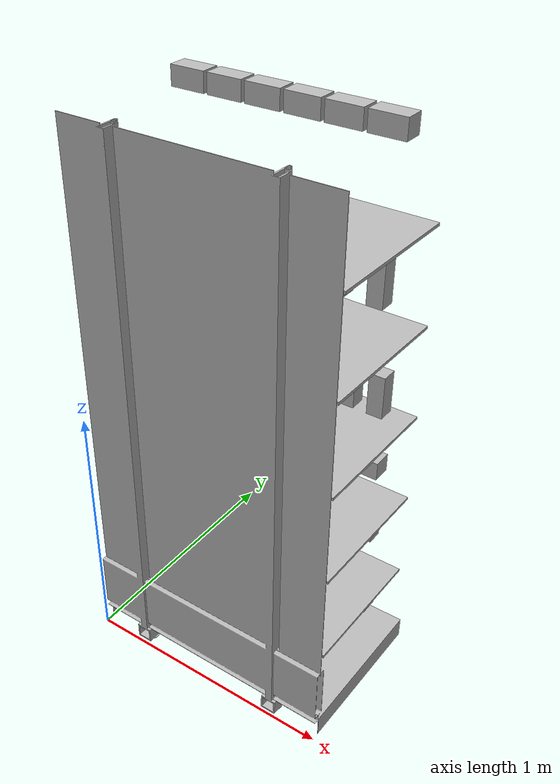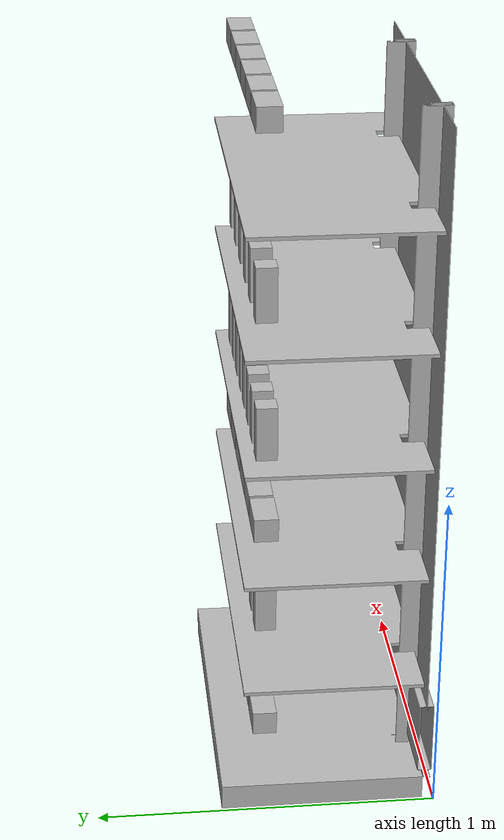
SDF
<?xml version="1.0"?>
<sdf version='1.6'>
  <model name='AH_shelf_filled_april'>
    <static>1</static>
    <link name='link'>
      <inertial>
        <mass>1</mass>
        <inertia>
          <ixx>1</ixx>
          <ixy>0</ixy>
          <ixz>0</ixz>
          <iyy>1</iyy>
          <iyz>0</iyz>
          <izz>1</izz>
        </inertia>
      </inertial>
      <pose frame=''>-0 0 0 0 0 0</pose>

      <visual name='visual'>
        <pose frame=''>0 0 0 0 0 0</pose>
        <geometry>
          <mesh>
            <uri>model://AH_shelf/AH_shelf.dae</uri>
            <scale>1 1 1</scale>
          </mesh>
        </geometry>
        <transparency>0</transparency>
        <cast_shadows>1</cast_shadows>
      </visual>

      <collision name='collision'>
        <laser_retro>0</laser_retro>
        <max_contacts>10</max_contacts>
        <pose frame=''>0 0 0 0 -0 0</pose>
        <geometry>
          <mesh>
            <uri>model://AH_shelf/AH_shelf.dae</uri>
            <scale>1 1 1</scale>
          </mesh>
        </geometry>
        <surface>
          <friction>
            <ode>
              <mu>1</mu>
              <mu2>1</mu2>
              <fdir1>0 0 0</fdir1>
              <slip1>0</slip1>
              <slip2>0</slip2>
            </ode>
            <torsional>
              <coefficient>1</coefficient>
              <patch_radius>0</patch_radius>
              <surface_radius>0</surface_radius>
              <use_patch_radius>1</use_patch_radius>
              <ode>
                <slip>0</slip>
              </ode>
            </torsional>
          </friction>
          <bounce>
            <restitution_coefficient>0</restitution_coefficient>
            <threshold>1e+06</threshold>
          </bounce>
          <contact>
            <collide_without_contact>0</collide_without_contact>
            <collide_without_contact_bitmask>1</collide_without_contact_bitmask>
            <collide_bitmask>1</collide_bitmask>
            <ode>
              <soft_cfm>0</soft_cfm>
              <soft_erp>0.2</soft_erp>
              <kp>1e+13</kp>
              <kd>1</kd>
              <max_vel>0.01</max_vel>
              <min_depth>0</min_depth>
            </ode>
            <bullet>
              <split_impulse>1</split_impulse>
              <split_impulse_penetration_threshold>-0.01</split_impulse_penetration_threshold>
              <soft_cfm>0</soft_cfm>
              <soft_erp>0.2</soft_erp>
              <kp>1e+13</kp>
              <kd>1</kd>
            </bullet>
          </contact>
        </surface>
      </collision>
    </link>

  <model name="board0">
    <pose>0 0.5 2.1 0 0 0</pose>

    <include>
      <uri>model://AH_thee_mango_tag36_11_00030</uri>
      <pose>0.14285714285714285 0 0 0 0 1.57</pose>
    </include>

    <include>
      <uri>model://AH_thee_mango_tag36_11_00031</uri>
      <pose>0.2857142857142857 0 0 0 0 1.57</pose>
    </include>

    <include>
      <uri>model://AH_thee_mango_tag36_11_00032</uri>
      <pose>0.42857142857142855 0 0 0 0 1.57</pose>
    </include>

    <include>
      <uri>model://AH_thee_mango_tag36_11_00033</uri>
      <pose>0.5714285714285714 0 0 0 0 1.57</pose>
    </include>

    <include>
      <uri>model://AH_thee_mango_tag36_11_00034</uri>
      <pose>0.7142857142857142 0 0 0 0 1.57</pose>
    </include>

    <include>
      <uri>model://AH_thee_mango_tag36_11_00035</uri>
      <pose>0.8571428571428571 0 0 0 0 1.57</pose>
    </include>

  </model>

  <model name="board1">
    <pose>0 0.5 1.6 0 0 0</pose>

    <include>
      <uri>model://AH_hagelslag_melk_tag36_11_00000</uri>
      <pose>0.14285714285714285 0 0 0 0 1.57</pose>
    </include>

    <include>
      <uri>model://AH_hagelslag_melk_tag36_11_00001</uri>
      <pose>0.2857142857142857 0 0 0 0 1.57</pose>
    </include>

    <include>
      <uri>model://AH_hagelslag_melk_tag36_11_00002</uri>
      <pose>0.42857142857142855 0 0 0 0 1.57</pose>
    </include>

    <include>
      <uri>model://AH_hagelslag_melk_tag36_11_00003</uri>
      <pose>0.5714285714285714 0 0 0 0 1.57</pose>
    </include>

    <include>
      <uri>model://AH_hagelslag_melk_tag36_11_00004</uri>
      <pose>0.7142857142857142 0 0 0 0 1.57</pose>
    </include>

    <include>
      <uri>model://AH_hagelslag_melk_tag36_11_00005</uri>
      <pose>0.8571428571428571 0 0 0 0 1.57</pose>
    </include>

  </model>

  <model name="board2">
    <pose>0 0.5 1.2 0 0 0</pose>

    <include>
      <uri>model://AH_hagelslag_puur_tag36_11_00015</uri>
      <pose>0.1111111111111111 0 0 0 0 1.57</pose>
    </include>

    <include>
      <uri>model://AH_hagelslag_puur_tag36_11_00016</uri>
      <pose>0.2222222222222222 0 0 0 0 1.57</pose>
    </include>

    <include>
      <uri>model://AH_hagelslag_puur_tag36_11_00017</uri>
      <pose>0.3333333333333333 0 0 0 0 1.57</pose>
    </include>

    <include>
      <uri>model://AH_hagelslag_puur_tag36_11_00018</uri>
      <pose>0.4444444444444444 0 0 0 0 1.57</pose>
    </include>

    <include>
      <uri>model://AH_hagelslag_puur_tag36_11_00019</uri>
      <pose>0.5555555555555556 0 0 0 0 1.57</pose>
    </include>

    <include>
      <uri>model://AH_hagelslag_puur_tag36_11_00020</uri>
      <pose>0.6666666666666666 0 0 0 0 1.57</pose>
    </include>

    <include>
      <uri>model://AH_hagelslag_puur_tag36_11_00021</uri>
      <pose>0.7777777777777777 0 0 0 0 1.57</pose>
    </include>

    <include>
      <uri>model://AH_hagelslag_puur_tag36_11_00022</uri>
      <pose>0.8888888888888888 0 0 0 0 1.57</pose>
    </include>

  </model>

  <model name="board3">
    <pose>0 0.5 0.9 0 0 0</pose>

    <include>
      <uri>model://AH_thee_mango_tag36_11_00030</uri>
      <pose>0.14285714285714285 0 0 0 0 1.57</pose>
    </include>

    <include>
      <uri>model://AH_thee_mango_tag36_11_00031</uri>
      <pose>0.2857142857142857 0 0 0 0 1.57</pose>
    </include>

    <include>
      <uri>model://AH_thee_mango_tag36_11_00032</uri>
      <pose>0.42857142857142855 0 0 0 0 1.57</pose>
    </include>

    <include>
      <uri>model://AH_thee_mango_tag36_11_00033</uri>
      <pose>0.5714285714285714 0 0 0 0 1.57</pose>
    </include>

    <include>
      <uri>model://AH_thee_mango_tag36_11_00034</uri>
      <pose>0.7142857142857142 0 0 0 0 1.57</pose>
    </include>

    <include>
      <uri>model://AH_thee_mango_tag36_11_00035</uri>
      <pose>0.8571428571428571 0 0 0 0 1.57</pose>
    </include>

  </model>

  <model name="board4">
    <pose>0 0.5 0.65 0 0 0</pose>

    <include>
      <uri>model://AH_hagelslag_melk_tag36_11_00000</uri>
      <pose>0.1111111111111111 0 0 0 0 1.57</pose>
    </include>

    <include>
      <uri>model://AH_hagelslag_melk_tag36_11_00001</uri>
      <pose>0.2222222222222222 0 0 0 0 1.57</pose>
    </include>

    <include>
      <uri>model://AH_hagelslag_melk_tag36_11_00002</uri>
      <pose>0.3333333333333333 0 0 0 0 1.57</pose>
    </include>

    <include>
      <uri>model://AH_hagelslag_melk_tag36_11_00003</uri>
      <pose>0.4444444444444444 0 0 0 0 1.57</pose>
    </include>

    <include>
      <uri>model://AH_hagelslag_melk_tag36_11_00004</uri>
      <pose>0.5555555555555556 0 0 0 0 1.57</pose>
    </include>

    <include>
      <uri>model://AH_hagelslag_melk_tag36_11_00005</uri>
      <pose>0.6666666666666666 0 0 0 0 1.57</pose>
    </include>

    <include>
      <uri>model://AH_hagelslag_melk_tag36_11_00006</uri>
      <pose>0.7777777777777777 0 0 0 0 1.57</pose>
    </include>

    <include>
      <uri>model://AH_hagelslag_melk_tag36_11_00007</uri>
      <pose>0.8888888888888888 0 0 0 0 1.57</pose>
    </include>

  </model>

  <model name="board5">
    <pose>0 0.5 0.25 0 0 0</pose>

    <include>
      <uri>model://AH_thee_bosvruchten_tag36_11_00045</uri>
      <pose>0.14285714285714285 0 0 0 0 1.57</pose>
    </include>

    <include>
      <uri>model://AH_thee_bosvruchten_tag36_11_00046</uri>
      <pose>0.2857142857142857 0 0 0 0 1.57</pose>
    </include>

    <include>
      <uri>model://AH_thee_bosvruchten_tag36_11_00047</uri>
      <pose>0.42857142857142855 0 0 0 0 1.57</pose>
    </include>

    <include>
      <uri>model://AH_thee_bosvruchten_tag36_11_00048</uri>
      <pose>0.5714285714285714 0 0 0 0 1.57</pose>
    </include>

    <include>
      <uri>model://AH_thee_bosvruchten_tag36_11_00049</uri>
      <pose>0.7142857142857142 0 0 0 0 1.57</pose>
    </include>

    <include>
      <uri>model://AH_thee_bosvruchten_tag36_11_00050</uri>
      <pose>0.8571428571428571 0 0 0 0 1.57</pose>
    </include>

  </model>

  </model>
</sdf>

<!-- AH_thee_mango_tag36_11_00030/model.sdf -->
<sdf version='1.6'>
  <model name='AH_thee_mango_tag36_11_00030'>
    <static>0</static>
    <link name='link_0'>

      <inertial>
        <mass>0.1</mass>
        <inertia>
          <ixx>1.4e-03</ixx>
          <ixy>0</ixy>
          <ixz>0</ixz>
          <iyy>1.4e-03</iyy>
          <iyz>0</iyz>
          <izz>2.8e-03</izz>
        </inertia>
      </inertial>

      <pose frame=''>-0 0 0 0 -0 0</pose>

      <visual name='visual'>
        <pose frame=''>0 0 0 0 -0 0</pose>
        <geometry>
          <mesh>
            <uri>model://AH_thee_mango/AH_thee_mango_tag36_11_00030/AH_thee_mango_tag36_11_00030.dae</uri>
            <scale>1 1 1</scale>
          </mesh>
        </geometry>
        <transparency>0</transparency>
        <cast_shadows>1</cast_shadows>
      </visual>

      <collision name='collision'>
        <laser_retro>0</laser_retro>
        <max_contacts>10</max_contacts>
        <pose frame=''>0 0 0 0 -0 0</pose>
        <geometry>
          <mesh>
            <uri>model://AH_thee_mango/AH_thee_mango_tag36_11_00030/AH_thee_mango_tag36_11_00030.dae</uri>
            <scale>1 1 1</scale>
          </mesh>
        </geometry>
        <surface>
          <friction>
            <ode>
              <mu>1</mu>
              <mu2>1</mu2>
              <fdir1>0 0 0</fdir1>
              <slip1>0</slip1>
              <slip2>0</slip2>
            </ode>
            <torsional>
              <coefficient>1</coefficient>
              <patch_radius>0</patch_radius>
              <surface_radius>0</surface_radius>
              <use_patch_radius>1</use_patch_radius>
              <ode>
                <slip>0</slip>
              </ode>
            </torsional>
          </friction>
          <bounce>
            <restitution_coefficient>0</restitution_coefficient>
            <threshold>1e+06</threshold>
          </bounce>
          <contact>
            <collide_without_contact>0</collide_without_contact>
            <collide_without_contact_bitmask>1</collide_without_contact_bitmask>
            <collide_bitmask>1</collide_bitmask>
            <ode>
              <soft_cfm>0</soft_cfm>
              <soft_erp>0.2</soft_erp>
              <kp>1e+13</kp>
              <kd>1</kd>
              <max_vel>0.01</max_vel>
              <min_depth>0</min_depth>
            </ode>
            <bullet>
              <split_impulse>1</split_impulse>
              <split_impulse_penetration_threshold>-0.01</split_impulse_penetration_threshold>
              <soft_cfm>0</soft_cfm>
              <soft_erp>0.2</soft_erp>
              <kp>1e+13</kp>
              <kd>1</kd>
            </bullet>
          </contact>
        </surface>
      </collision>

    </link>
  </model>
</sdf>

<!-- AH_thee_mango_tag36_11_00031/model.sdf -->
<sdf version='1.6'>
  <model name='AH_thee_mango_tag36_11_00031'>
    <static>0</static>
    <link name='link_0'>

      <inertial>
        <mass>0.1</mass>
        <inertia>
          <ixx>1.4e-03</ixx>
          <ixy>0</ixy>
          <ixz>0</ixz>
          <iyy>1.4e-03</iyy>
          <iyz>0</iyz>
          <izz>2.8e-03</izz>
        </inertia>
      </inertial>

      <pose frame=''>-0 0 0 0 -0 0</pose>

      <visual name='visual'>
        <pose frame=''>0 0 0 0 -0 0</pose>
        <geometry>
          <mesh>
            <uri>model://AH_thee_mango/AH_thee_mango_tag36_11_00031/AH_thee_mango_tag36_11_00031.dae</uri>
            <scale>1 1 1</scale>
          </mesh>
        </geometry>
        <transparency>0</transparency>
        <cast_shadows>1</cast_shadows>
      </visual>

      <collision name='collision'>
        <laser_retro>0</laser_retro>
        <max_contacts>10</max_contacts>
        <pose frame=''>0 0 0 0 -0 0</pose>
        <geometry>
          <mesh>
            <uri>model://AH_thee_mango/AH_thee_mango_tag36_11_00031/AH_thee_mango_tag36_11_00031.dae</uri>
            <scale>1 1 1</scale>
          </mesh>
        </geometry>
        <surface>
          <friction>
            <ode>
              <mu>1</mu>
              <mu2>1</mu2>
              <fdir1>0 0 0</fdir1>
              <slip1>0</slip1>
              <slip2>0</slip2>
            </ode>
            <torsional>
              <coefficient>1</coefficient>
              <patch_radius>0</patch_radius>
              <surface_radius>0</surface_radius>
              <use_patch_radius>1</use_patch_radius>
              <ode>
                <slip>0</slip>
              </ode>
            </torsional>
          </friction>
          <bounce>
            <restitution_coefficient>0</restitution_coefficient>
            <threshold>1e+06</threshold>
          </bounce>
          <contact>
            <collide_without_contact>0</collide_without_contact>
            <collide_without_contact_bitmask>1</collide_without_contact_bitmask>
            <collide_bitmask>1</collide_bitmask>
            <ode>
              <soft_cfm>0</soft_cfm>
              <soft_erp>0.2</soft_erp>
              <kp>1e+13</kp>
              <kd>1</kd>
              <max_vel>0.01</max_vel>
              <min_depth>0</min_depth>
            </ode>
            <bullet>
              <split_impulse>1</split_impulse>
              <split_impulse_penetration_threshold>-0.01</split_impulse_penetration_threshold>
              <soft_cfm>0</soft_cfm>
              <soft_erp>0.2</soft_erp>
              <kp>1e+13</kp>
              <kd>1</kd>
            </bullet>
          </contact>
        </surface>
      </collision>

    </link>
  </model>
</sdf>

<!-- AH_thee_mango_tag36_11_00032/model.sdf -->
<sdf version='1.6'>
  <model name='AH_thee_mango_tag36_11_00032'>
    <static>0</static>
    <link name='link_0'>

      <inertial>
        <mass>0.1</mass>
        <inertia>
          <ixx>1.4e-03</ixx>
          <ixy>0</ixy>
          <ixz>0</ixz>
          <iyy>1.4e-03</iyy>
          <iyz>0</iyz>
          <izz>2.8e-03</izz>
        </inertia>
      </inertial>

      <pose frame=''>-0 0 0 0 -0 0</pose>

      <visual name='visual'>
        <pose frame=''>0 0 0 0 -0 0</pose>
        <geometry>
          <mesh>
            <uri>model://AH_thee_mango/AH_thee_mango_tag36_11_00032/AH_thee_mango_tag36_11_00032.dae</uri>
            <scale>1 1 1</scale>
          </mesh>
        </geometry>
        <transparency>0</transparency>
        <cast_shadows>1</cast_shadows>
      </visual>

      <collision name='collision'>
        <laser_retro>0</laser_retro>
        <max_contacts>10</max_contacts>
        <pose frame=''>0 0 0 0 -0 0</pose>
        <geometry>
          <mesh>
            <uri>model://AH_thee_mango/AH_thee_mango_tag36_11_00032/AH_thee_mango_tag36_11_00032.dae</uri>
            <scale>1 1 1</scale>
          </mesh>
        </geometry>
        <surface>
          <friction>
            <ode>
              <mu>1</mu>
              <mu2>1</mu2>
              <fdir1>0 0 0</fdir1>
              <slip1>0</slip1>
              <slip2>0</slip2>
            </ode>
            <torsional>
              <coefficient>1</coefficient>
              <patch_radius>0</patch_radius>
              <surface_radius>0</surface_radius>
              <use_patch_radius>1</use_patch_radius>
              <ode>
                <slip>0</slip>
              </ode>
            </torsional>
          </friction>
          <bounce>
            <restitution_coefficient>0</restitution_coefficient>
            <threshold>1e+06</threshold>
          </bounce>
          <contact>
            <collide_without_contact>0</collide_without_contact>
            <collide_without_contact_bitmask>1</collide_without_contact_bitmask>
            <collide_bitmask>1</collide_bitmask>
            <ode>
              <soft_cfm>0</soft_cfm>
              <soft_erp>0.2</soft_erp>
              <kp>1e+13</kp>
              <kd>1</kd>
              <max_vel>0.01</max_vel>
              <min_depth>0</min_depth>
            </ode>
            <bullet>
              <split_impulse>1</split_impulse>
              <split_impulse_penetration_threshold>-0.01</split_impulse_penetration_threshold>
              <soft_cfm>0</soft_cfm>
              <soft_erp>0.2</soft_erp>
              <kp>1e+13</kp>
              <kd>1</kd>
            </bullet>
          </contact>
        </surface>
      </collision>

    </link>
  </model>
</sdf>

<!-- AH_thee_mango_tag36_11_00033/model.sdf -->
<sdf version='1.6'>
  <model name='AH_thee_mango_tag36_11_00033'>
    <static>0</static>
    <link name='link_0'>

      <inertial>
        <mass>0.1</mass>
        <inertia>
          <ixx>1.4e-03</ixx>
          <ixy>0</ixy>
          <ixz>0</ixz>
          <iyy>1.4e-03</iyy>
          <iyz>0</iyz>
          <izz>2.8e-03</izz>
        </inertia>
      </inertial>

      <pose frame=''>-0 0 0 0 -0 0</pose>

      <visual name='visual'>
        <pose frame=''>0 0 0 0 -0 0</pose>
        <geometry>
          <mesh>
            <uri>model://AH_thee_mango/AH_thee_mango_tag36_11_00033/AH_thee_mango_tag36_11_00033.dae</uri>
            <scale>1 1 1</scale>
          </mesh>
        </geometry>
        <transparency>0</transparency>
        <cast_shadows>1</cast_shadows>
      </visual>

      <collision name='collision'>
        <laser_retro>0</laser_retro>
        <max_contacts>10</max_contacts>
        <pose frame=''>0 0 0 0 -0 0</pose>
        <geometry>
          <mesh>
            <uri>model://AH_thee_mango/AH_thee_mango_tag36_11_00033/AH_thee_mango_tag36_11_00033.dae</uri>
            <scale>1 1 1</scale>
          </mesh>
        </geometry>
        <surface>
          <friction>
            <ode>
              <mu>1</mu>
              <mu2>1</mu2>
              <fdir1>0 0 0</fdir1>
              <slip1>0</slip1>
              <slip2>0</slip2>
            </ode>
            <torsional>
              <coefficient>1</coefficient>
              <patch_radius>0</patch_radius>
              <surface_radius>0</surface_radius>
              <use_patch_radius>1</use_patch_radius>
              <ode>
                <slip>0</slip>
              </ode>
            </torsional>
          </friction>
          <bounce>
            <restitution_coefficient>0</restitution_coefficient>
            <threshold>1e+06</threshold>
          </bounce>
          <contact>
            <collide_without_contact>0</collide_without_contact>
            <collide_without_contact_bitmask>1</collide_without_contact_bitmask>
            <collide_bitmask>1</collide_bitmask>
            <ode>
              <soft_cfm>0</soft_cfm>
              <soft_erp>0.2</soft_erp>
              <kp>1e+13</kp>
              <kd>1</kd>
              <max_vel>0.01</max_vel>
              <min_depth>0</min_depth>
            </ode>
            <bullet>
              <split_impulse>1</split_impulse>
              <split_impulse_penetration_threshold>-0.01</split_impulse_penetration_threshold>
              <soft_cfm>0</soft_cfm>
              <soft_erp>0.2</soft_erp>
              <kp>1e+13</kp>
              <kd>1</kd>
            </bullet>
          </contact>
        </surface>
      </collision>

    </link>
  </model>
</sdf>

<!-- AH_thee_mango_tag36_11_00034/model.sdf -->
<sdf version='1.6'>
  <model name='AH_thee_mango_tag36_11_00034'>
    <static>0</static>
    <link name='link_0'>

      <inertial>
        <mass>0.1</mass>
        <inertia>
          <ixx>1.4e-03</ixx>
          <ixy>0</ixy>
          <ixz>0</ixz>
          <iyy>1.4e-03</iyy>
          <iyz>0</iyz>
          <izz>2.8e-03</izz>
        </inertia>
      </inertial>

      <pose frame=''>-0 0 0 0 -0 0</pose>

      <visual name='visual'>
        <pose frame=''>0 0 0 0 -0 0</pose>
        <geometry>
          <mesh>
            <uri>model://AH_thee_mango/AH_thee_mango_tag36_11_00034/AH_thee_mango_tag36_11_00034.dae</uri>
            <scale>1 1 1</scale>
          </mesh>
        </geometry>
        <transparency>0</transparency>
        <cast_shadows>1</cast_shadows>
      </visual>

      <collision name='collision'>
        <laser_retro>0</laser_retro>
        <max_contacts>10</max_contacts>
        <pose frame=''>0 0 0 0 -0 0</pose>
        <geometry>
          <mesh>
            <uri>model://AH_thee_mango/AH_thee_mango_tag36_11_00034/AH_thee_mango_tag36_11_00034.dae</uri>
            <scale>1 1 1</scale>
          </mesh>
        </geometry>
        <surface>
          <friction>
            <ode>
              <mu>1</mu>
              <mu2>1</mu2>
              <fdir1>0 0 0</fdir1>
              <slip1>0</slip1>
              <slip2>0</slip2>
            </ode>
            <torsional>
              <coefficient>1</coefficient>
              <patch_radius>0</patch_radius>
              <surface_radius>0</surface_radius>
              <use_patch_radius>1</use_patch_radius>
              <ode>
                <slip>0</slip>
              </ode>
            </torsional>
          </friction>
          <bounce>
            <restitution_coefficient>0</restitution_coefficient>
            <threshold>1e+06</threshold>
          </bounce>
          <contact>
            <collide_without_contact>0</collide_without_contact>
            <collide_without_contact_bitmask>1</collide_without_contact_bitmask>
            <collide_bitmask>1</collide_bitmask>
            <ode>
              <soft_cfm>0</soft_cfm>
              <soft_erp>0.2</soft_erp>
              <kp>1e+13</kp>
              <kd>1</kd>
              <max_vel>0.01</max_vel>
              <min_depth>0</min_depth>
            </ode>
            <bullet>
              <split_impulse>1</split_impulse>
              <split_impulse_penetration_threshold>-0.01</split_impulse_penetration_threshold>
              <soft_cfm>0</soft_cfm>
              <soft_erp>0.2</soft_erp>
              <kp>1e+13</kp>
              <kd>1</kd>
            </bullet>
          </contact>
        </surface>
      </collision>

    </link>
  </model>
</sdf>

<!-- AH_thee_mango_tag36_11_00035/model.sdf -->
<sdf version='1.6'>
  <model name='AH_thee_mango_tag36_11_00035'>
    <static>0</static>
    <link name='link_0'>

      <inertial>
        <mass>0.1</mass>
        <inertia>
          <ixx>1.4e-03</ixx>
          <ixy>0</ixy>
          <ixz>0</ixz>
          <iyy>1.4e-03</iyy>
          <iyz>0</iyz>
          <izz>2.8e-03</izz>
        </inertia>
      </inertial>

      <pose frame=''>-0 0 0 0 -0 0</pose>

      <visual name='visual'>
        <pose frame=''>0 0 0 0 -0 0</pose>
        <geometry>
          <mesh>
            <uri>model://AH_thee_mango/AH_thee_mango_tag36_11_00035/AH_thee_mango_tag36_11_00035.dae</uri>
            <scale>1 1 1</scale>
          </mesh>
        </geometry>
        <transparency>0</transparency>
        <cast_shadows>1</cast_shadows>
      </visual>

      <collision name='collision'>
        <laser_retro>0</laser_retro>
        <max_contacts>10</max_contacts>
        <pose frame=''>0 0 0 0 -0 0</pose>
        <geometry>
          <mesh>
            <uri>model://AH_thee_mango/AH_thee_mango_tag36_11_00035/AH_thee_mango_tag36_11_00035.dae</uri>
            <scale>1 1 1</scale>
          </mesh>
        </geometry>
        <surface>
          <friction>
            <ode>
              <mu>1</mu>
              <mu2>1</mu2>
              <fdir1>0 0 0</fdir1>
              <slip1>0</slip1>
              <slip2>0</slip2>
            </ode>
            <torsional>
              <coefficient>1</coefficient>
              <patch_radius>0</patch_radius>
              <surface_radius>0</surface_radius>
              <use_patch_radius>1</use_patch_radius>
              <ode>
                <slip>0</slip>
              </ode>
            </torsional>
          </friction>
          <bounce>
            <restitution_coefficient>0</restitution_coefficient>
            <threshold>1e+06</threshold>
          </bounce>
          <contact>
            <collide_without_contact>0</collide_without_contact>
            <collide_without_contact_bitmask>1</collide_without_contact_bitmask>
            <collide_bitmask>1</collide_bitmask>
            <ode>
              <soft_cfm>0</soft_cfm>
              <soft_erp>0.2</soft_erp>
              <kp>1e+13</kp>
              <kd>1</kd>
              <max_vel>0.01</max_vel>
              <min_depth>0</min_depth>
            </ode>
            <bullet>
              <split_impulse>1</split_impulse>
              <split_impulse_penetration_threshold>-0.01</split_impulse_penetration_threshold>
              <soft_cfm>0</soft_cfm>
              <soft_erp>0.2</soft_erp>
              <kp>1e+13</kp>
              <kd>1</kd>
            </bullet>
          </contact>
        </surface>
      </collision>

    </link>
  </model>
</sdf>

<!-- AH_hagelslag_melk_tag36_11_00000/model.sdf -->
<sdf version='1.6'>
  <model name='AH_hagelslag_melk_tag36_11_00000'>
    <static>0</static>
    <link name='link_0'>

      <inertial>
        <mass>0.1</mass>
        <inertia>
          <ixx>1.4e-03</ixx>
          <ixy>0</ixy>
          <ixz>0</ixz>
          <iyy>1.4e-03</iyy>
          <iyz>0</iyz>
          <izz>2.8e-03</izz>
        </inertia>
      </inertial>

      <pose frame=''>-0 0 0 0 -0 0</pose>

      <visual name='visual'>
        <pose frame=''>0 0 0 0 -0 0</pose>
        <geometry>
          <mesh>
            <uri>model://AH_hagelslag_melk/AH_hagelslag_melk_tag36_11_00000/AH_hagelslag_melk_tag36_11_00000.dae</uri>
            <scale>1 1 1</scale>
          </mesh>
        </geometry>
        <transparency>0</transparency>
        <cast_shadows>1</cast_shadows>
      </visual>

      <collision name='collision'>
        <laser_retro>0</laser_retro>
        <max_contacts>10</max_contacts>
        <pose frame=''>0 0 0 0 -0 0</pose>
        <geometry>
          <mesh>
            <uri>model://AH_hagelslag_melk/AH_hagelslag_melk_tag36_11_00000/AH_hagelslag_melk_tag36_11_00000.dae</uri>
            <scale>1 1 1</scale>
          </mesh>
        </geometry>
        <surface>
          <friction>
            <ode>
              <mu>1</mu>
              <mu2>1</mu2>
              <fdir1>0 0 0</fdir1>
              <slip1>0</slip1>
              <slip2>0</slip2>
            </ode>
            <torsional>
              <coefficient>1</coefficient>
              <patch_radius>0</patch_radius>
              <surface_radius>0</surface_radius>
              <use_patch_radius>1</use_patch_radius>
              <ode>
                <slip>0</slip>
              </ode>
            </torsional>
          </friction>
          <bounce>
            <restitution_coefficient>0</restitution_coefficient>
            <threshold>1e+06</threshold>
          </bounce>
          <contact>
            <collide_without_contact>0</collide_without_contact>
            <collide_without_contact_bitmask>1</collide_without_contact_bitmask>
            <collide_bitmask>1</collide_bitmask>
            <ode>
              <soft_cfm>0</soft_cfm>
              <soft_erp>0.2</soft_erp>
              <kp>1e+13</kp>
              <kd>1</kd>
              <max_vel>0.01</max_vel>
              <min_depth>0</min_depth>
            </ode>
            <bullet>
              <split_impulse>1</split_impulse>
              <split_impulse_penetration_threshold>-0.01</split_impulse_penetration_threshold>
              <soft_cfm>0</soft_cfm>
              <soft_erp>0.2</soft_erp>
              <kp>1e+13</kp>
              <kd>1</kd>
            </bullet>
          </contact>
        </surface>
      </collision>

    </link>
  </model>
</sdf>

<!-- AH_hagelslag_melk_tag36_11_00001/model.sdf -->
<sdf version='1.6'>
  <model name='AH_hagelslag_melk_tag36_11_00001'>
    <static>0</static>
    <link name='link_0'>

      <inertial>
        <mass>0.1</mass>
        <inertia>
          <ixx>1.4e-03</ixx>
          <ixy>0</ixy>
          <ixz>0</ixz>
          <iyy>1.4e-03</iyy>
          <iyz>0</iyz>
          <izz>2.8e-03</izz>
        </inertia>
      </inertial>

      <pose frame=''>-0 0 0 0 -0 0</pose>

      <visual name='visual'>
        <pose frame=''>0 0 0 0 -0 0</pose>
        <geometry>
          <mesh>
            <uri>model://AH_hagelslag_melk/AH_hagelslag_melk_tag36_11_00001/AH_hagelslag_melk_tag36_11_00001.dae</uri>
            <scale>1 1 1</scale>
          </mesh>
        </geometry>
        <transparency>0</transparency>
        <cast_shadows>1</cast_shadows>
      </visual>

      <collision name='collision'>
        <laser_retro>0</laser_retro>
        <max_contacts>10</max_contacts>
        <pose frame=''>0 0 0 0 -0 0</pose>
        <geometry>
          <mesh>
            <uri>model://AH_hagelslag_melk/AH_hagelslag_melk_tag36_11_00001/AH_hagelslag_melk_tag36_11_00001.dae</uri>
            <scale>1 1 1</scale>
          </mesh>
        </geometry>
        <surface>
          <friction>
            <ode>
              <mu>1</mu>
              <mu2>1</mu2>
              <fdir1>0 0 0</fdir1>
              <slip1>0</slip1>
              <slip2>0</slip2>
            </ode>
            <torsional>
              <coefficient>1</coefficient>
              <patch_radius>0</patch_radius>
              <surface_radius>0</surface_radius>
              <use_patch_radius>1</use_patch_radius>
              <ode>
                <slip>0</slip>
              </ode>
            </torsional>
          </friction>
          <bounce>
            <restitution_coefficient>0</restitution_coefficient>
            <threshold>1e+06</threshold>
          </bounce>
          <contact>
            <collide_without_contact>0</collide_without_contact>
            <collide_without_contact_bitmask>1</collide_without_contact_bitmask>
            <collide_bitmask>1</collide_bitmask>
            <ode>
              <soft_cfm>0</soft_cfm>
              <soft_erp>0.2</soft_erp>
              <kp>1e+13</kp>
              <kd>1</kd>
              <max_vel>0.01</max_vel>
              <min_depth>0</min_depth>
            </ode>
            <bullet>
              <split_impulse>1</split_impulse>
              <split_impulse_penetration_threshold>-0.01</split_impulse_penetration_threshold>
              <soft_cfm>0</soft_cfm>
              <soft_erp>0.2</soft_erp>
              <kp>1e+13</kp>
              <kd>1</kd>
            </bullet>
          </contact>
        </surface>
      </collision>

    </link>
  </model>
</sdf>

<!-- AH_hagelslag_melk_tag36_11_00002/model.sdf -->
<sdf version='1.6'>
  <model name='AH_hagelslag_melk_tag36_11_00002'>
    <static>0</static>
    <link name='link_0'>

      <inertial>
        <mass>0.1</mass>
        <inertia>
          <ixx>1.4e-03</ixx>
          <ixy>0</ixy>
          <ixz>0</ixz>
          <iyy>1.4e-03</iyy>
          <iyz>0</iyz>
          <izz>2.8e-03</izz>
        </inertia>
      </inertial>

      <pose frame=''>-0 0 0 0 -0 0</pose>

      <visual name='visual'>
        <pose frame=''>0 0 0 0 -0 0</pose>
        <geometry>
          <mesh>
            <uri>model://AH_hagelslag_melk/AH_hagelslag_melk_tag36_11_00002/AH_hagelslag_melk_tag36_11_00002.dae</uri>
            <scale>1 1 1</scale>
          </mesh>
        </geometry>
        <transparency>0</transparency>
        <cast_shadows>1</cast_shadows>
      </visual>

      <collision name='collision'>
        <laser_retro>0</laser_retro>
        <max_contacts>10</max_contacts>
        <pose frame=''>0 0 0 0 -0 0</pose>
        <geometry>
          <mesh>
            <uri>model://AH_hagelslag_melk/AH_hagelslag_melk_tag36_11_00002/AH_hagelslag_melk_tag36_11_00002.dae</uri>
            <scale>1 1 1</scale>
          </mesh>
        </geometry>
        <surface>
          <friction>
            <ode>
              <mu>1</mu>
              <mu2>1</mu2>
              <fdir1>0 0 0</fdir1>
              <slip1>0</slip1>
              <slip2>0</slip2>
            </ode>
            <torsional>
              <coefficient>1</coefficient>
              <patch_radius>0</patch_radius>
              <surface_radius>0</surface_radius>
              <use_patch_radius>1</use_patch_radius>
              <ode>
                <slip>0</slip>
              </ode>
            </torsional>
          </friction>
          <bounce>
            <restitution_coefficient>0</restitution_coefficient>
            <threshold>1e+06</threshold>
          </bounce>
          <contact>
            <collide_without_contact>0</collide_without_contact>
            <collide_without_contact_bitmask>1</collide_without_contact_bitmask>
            <collide_bitmask>1</collide_bitmask>
            <ode>
              <soft_cfm>0</soft_cfm>
              <soft_erp>0.2</soft_erp>
              <kp>1e+13</kp>
              <kd>1</kd>
              <max_vel>0.01</max_vel>
              <min_depth>0</min_depth>
            </ode>
            <bullet>
              <split_impulse>1</split_impulse>
              <split_impulse_penetration_threshold>-0.01</split_impulse_penetration_threshold>
              <soft_cfm>0</soft_cfm>
              <soft_erp>0.2</soft_erp>
              <kp>1e+13</kp>
              <kd>1</kd>
            </bullet>
          </contact>
        </surface>
      </collision>

    </link>
  </model>
</sdf>

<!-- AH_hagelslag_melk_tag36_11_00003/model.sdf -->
<sdf version='1.6'>
  <model name='AH_hagelslag_melk_tag36_11_00003'>
    <static>0</static>
    <link name='link_0'>

      <inertial>
        <mass>0.1</mass>
        <inertia>
          <ixx>1.4e-03</ixx>
          <ixy>0</ixy>
          <ixz>0</ixz>
          <iyy>1.4e-03</iyy>
          <iyz>0</iyz>
          <izz>2.8e-03</izz>
        </inertia>
      </inertial>

      <pose frame=''>-0 0 0 0 -0 0</pose>

      <visual name='visual'>
        <pose frame=''>0 0 0 0 -0 0</pose>
        <geometry>
          <mesh>
            <uri>model://AH_hagelslag_melk/AH_hagelslag_melk_tag36_11_00003/AH_hagelslag_melk_tag36_11_00003.dae</uri>
            <scale>1 1 1</scale>
          </mesh>
        </geometry>
        <transparency>0</transparency>
        <cast_shadows>1</cast_shadows>
      </visual>

      <collision name='collision'>
        <laser_retro>0</laser_retro>
        <max_contacts>10</max_contacts>
        <pose frame=''>0 0 0 0 -0 0</pose>
        <geometry>
          <mesh>
            <uri>model://AH_hagelslag_melk/AH_hagelslag_melk_tag36_11_00003/AH_hagelslag_melk_tag36_11_00003.dae</uri>
            <scale>1 1 1</scale>
          </mesh>
        </geometry>
        <surface>
          <friction>
            <ode>
              <mu>1</mu>
              <mu2>1</mu2>
              <fdir1>0 0 0</fdir1>
              <slip1>0</slip1>
              <slip2>0</slip2>
            </ode>
            <torsional>
              <coefficient>1</coefficient>
              <patch_radius>0</patch_radius>
              <surface_radius>0</surface_radius>
              <use_patch_radius>1</use_patch_radius>
              <ode>
                <slip>0</slip>
              </ode>
            </torsional>
          </friction>
          <bounce>
            <restitution_coefficient>0</restitution_coefficient>
            <threshold>1e+06</threshold>
          </bounce>
          <contact>
            <collide_without_contact>0</collide_without_contact>
            <collide_without_contact_bitmask>1</collide_without_contact_bitmask>
            <collide_bitmask>1</collide_bitmask>
            <ode>
              <soft_cfm>0</soft_cfm>
              <soft_erp>0.2</soft_erp>
              <kp>1e+13</kp>
              <kd>1</kd>
              <max_vel>0.01</max_vel>
              <min_depth>0</min_depth>
            </ode>
            <bullet>
              <split_impulse>1</split_impulse>
              <split_impulse_penetration_threshold>-0.01</split_impulse_penetration_threshold>
              <soft_cfm>0</soft_cfm>
              <soft_erp>0.2</soft_erp>
              <kp>1e+13</kp>
              <kd>1</kd>
            </bullet>
          </contact>
        </surface>
      </collision>

    </link>
  </model>
</sdf>

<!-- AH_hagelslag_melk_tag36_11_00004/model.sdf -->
<sdf version='1.6'>
  <model name='AH_hagelslag_melk_tag36_11_00004'>
    <static>0</static>
    <link name='link_0'>

      <inertial>
        <mass>0.1</mass>
        <inertia>
          <ixx>1.4e-03</ixx>
          <ixy>0</ixy>
          <ixz>0</ixz>
          <iyy>1.4e-03</iyy>
          <iyz>0</iyz>
          <izz>2.8e-03</izz>
        </inertia>
      </inertial>

      <pose frame=''>-0 0 0 0 -0 0</pose>

      <visual name='visual'>
        <pose frame=''>0 0 0 0 -0 0</pose>
        <geometry>
          <mesh>
            <uri>model://AH_hagelslag_melk/AH_hagelslag_melk_tag36_11_00004/AH_hagelslag_melk_tag36_11_00004.dae</uri>
            <scale>1 1 1</scale>
          </mesh>
        </geometry>
        <transparency>0</transparency>
        <cast_shadows>1</cast_shadows>
      </visual>

      <collision name='collision'>
        <laser_retro>0</laser_retro>
        <max_contacts>10</max_contacts>
        <pose frame=''>0 0 0 0 -0 0</pose>
        <geometry>
          <mesh>
            <uri>model://AH_hagelslag_melk/AH_hagelslag_melk_tag36_11_00004/AH_hagelslag_melk_tag36_11_00004.dae</uri>
            <scale>1 1 1</scale>
          </mesh>
        </geometry>
        <surface>
          <friction>
            <ode>
              <mu>1</mu>
              <mu2>1</mu2>
              <fdir1>0 0 0</fdir1>
              <slip1>0</slip1>
              <slip2>0</slip2>
            </ode>
            <torsional>
              <coefficient>1</coefficient>
              <patch_radius>0</patch_radius>
              <surface_radius>0</surface_radius>
              <use_patch_radius>1</use_patch_radius>
              <ode>
                <slip>0</slip>
              </ode>
            </torsional>
          </friction>
          <bounce>
            <restitution_coefficient>0</restitution_coefficient>
            <threshold>1e+06</threshold>
          </bounce>
          <contact>
            <collide_without_contact>0</collide_without_contact>
            <collide_without_contact_bitmask>1</collide_without_contact_bitmask>
            <collide_bitmask>1</collide_bitmask>
            <ode>
              <soft_cfm>0</soft_cfm>
              <soft_erp>0.2</soft_erp>
              <kp>1e+13</kp>
              <kd>1</kd>
              <max_vel>0.01</max_vel>
              <min_depth>0</min_depth>
            </ode>
            <bullet>
              <split_impulse>1</split_impulse>
              <split_impulse_penetration_threshold>-0.01</split_impulse_penetration_threshold>
              <soft_cfm>0</soft_cfm>
              <soft_erp>0.2</soft_erp>
              <kp>1e+13</kp>
              <kd>1</kd>
            </bullet>
          </contact>
        </surface>
      </collision>

    </link>
  </model>
</sdf>

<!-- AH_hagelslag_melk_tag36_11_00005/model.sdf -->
<sdf version='1.6'>
  <model name='AH_hagelslag_melk_tag36_11_00005'>
    <static>0</static>
    <link name='link_0'>

      <inertial>
        <mass>0.1</mass>
        <inertia>
          <ixx>1.4e-03</ixx>
          <ixy>0</ixy>
          <ixz>0</ixz>
          <iyy>1.4e-03</iyy>
          <iyz>0</iyz>
          <izz>2.8e-03</izz>
        </inertia>
      </inertial>

      <pose frame=''>-0 0 0 0 -0 0</pose>

      <visual name='visual'>
        <pose frame=''>0 0 0 0 -0 0</pose>
        <geometry>
          <mesh>
            <uri>model://AH_hagelslag_melk/AH_hagelslag_melk_tag36_11_00005/AH_hagelslag_melk_tag36_11_00005.dae</uri>
            <scale>1 1 1</scale>
          </mesh>
        </geometry>
        <transparency>0</transparency>
        <cast_shadows>1</cast_shadows>
      </visual>

      <collision name='collision'>
        <laser_retro>0</laser_retro>
        <max_contacts>10</max_contacts>
        <pose frame=''>0 0 0 0 -0 0</pose>
        <geometry>
          <mesh>
            <uri>model://AH_hagelslag_melk/AH_hagelslag_melk_tag36_11_00005/AH_hagelslag_melk_tag36_11_00005.dae</uri>
            <scale>1 1 1</scale>
          </mesh>
        </geometry>
        <surface>
          <friction>
            <ode>
              <mu>1</mu>
              <mu2>1</mu2>
              <fdir1>0 0 0</fdir1>
              <slip1>0</slip1>
              <slip2>0</slip2>
            </ode>
            <torsional>
              <coefficient>1</coefficient>
              <patch_radius>0</patch_radius>
              <surface_radius>0</surface_radius>
              <use_patch_radius>1</use_patch_radius>
              <ode>
                <slip>0</slip>
              </ode>
            </torsional>
          </friction>
          <bounce>
            <restitution_coefficient>0</restitution_coefficient>
            <threshold>1e+06</threshold>
          </bounce>
          <contact>
            <collide_without_contact>0</collide_without_contact>
            <collide_without_contact_bitmask>1</collide_without_contact_bitmask>
            <collide_bitmask>1</collide_bitmask>
            <ode>
              <soft_cfm>0</soft_cfm>
              <soft_erp>0.2</soft_erp>
              <kp>1e+13</kp>
              <kd>1</kd>
              <max_vel>0.01</max_vel>
              <min_depth>0</min_depth>
            </ode>
            <bullet>
              <split_impulse>1</split_impulse>
              <split_impulse_penetration_threshold>-0.01</split_impulse_penetration_threshold>
              <soft_cfm>0</soft_cfm>
              <soft_erp>0.2</soft_erp>
              <kp>1e+13</kp>
              <kd>1</kd>
            </bullet>
          </contact>
        </surface>
      </collision>

    </link>
  </model>
</sdf>

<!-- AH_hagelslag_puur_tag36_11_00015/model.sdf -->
<sdf version='1.6'>
  <model name='AH_hagelslag_puur_tag36_11_00015'>
    <static>0</static>
    <link name='link_0'>

      <inertial>
        <mass>0.1</mass>
        <inertia>
          <ixx>1.4e-03</ixx>
          <ixy>0</ixy>
          <ixz>0</ixz>
          <iyy>1.4e-03</iyy>
          <iyz>0</iyz>
          <izz>2.8e-03</izz>
        </inertia>
      </inertial>

      <pose frame=''>-0 0 0 0 -0 0</pose>

      <visual name='visual'>
        <pose frame=''>0 0 0 0 -0 0</pose>
        <geometry>
          <mesh>
            <uri>model://AH_hagelslag_puur/AH_hagelslag_puur_tag36_11_00015/AH_hagelslag_puur_tag36_11_00015.dae</uri>
            <scale>1 1 1</scale>
          </mesh>
        </geometry>
        <transparency>0</transparency>
        <cast_shadows>1</cast_shadows>
      </visual>

      <collision name='collision'>
        <laser_retro>0</laser_retro>
        <max_contacts>10</max_contacts>
        <pose frame=''>0 0 0 0 -0 0</pose>
        <geometry>
          <mesh>
            <uri>model://AH_hagelslag_puur/AH_hagelslag_puur_tag36_11_00015/AH_hagelslag_puur_tag36_11_00015.dae</uri>
            <scale>1 1 1</scale>
          </mesh>
        </geometry>
        <surface>
          <friction>
            <ode>
              <mu>1</mu>
              <mu2>1</mu2>
              <fdir1>0 0 0</fdir1>
              <slip1>0</slip1>
              <slip2>0</slip2>
            </ode>
            <torsional>
              <coefficient>1</coefficient>
              <patch_radius>0</patch_radius>
              <surface_radius>0</surface_radius>
              <use_patch_radius>1</use_patch_radius>
              <ode>
                <slip>0</slip>
              </ode>
            </torsional>
          </friction>
          <bounce>
            <restitution_coefficient>0</restitution_coefficient>
            <threshold>1e+06</threshold>
          </bounce>
          <contact>
            <collide_without_contact>0</collide_without_contact>
            <collide_without_contact_bitmask>1</collide_without_contact_bitmask>
            <collide_bitmask>1</collide_bitmask>
            <ode>
              <soft_cfm>0</soft_cfm>
              <soft_erp>0.2</soft_erp>
              <kp>1e+13</kp>
              <kd>1</kd>
              <max_vel>0.01</max_vel>
              <min_depth>0</min_depth>
            </ode>
            <bullet>
              <split_impulse>1</split_impulse>
              <split_impulse_penetration_threshold>-0.01</split_impulse_penetration_threshold>
              <soft_cfm>0</soft_cfm>
              <soft_erp>0.2</soft_erp>
              <kp>1e+13</kp>
              <kd>1</kd>
            </bullet>
          </contact>
        </surface>
      </collision>

    </link>
  </model>
</sdf>

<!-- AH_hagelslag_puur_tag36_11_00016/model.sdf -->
<sdf version='1.6'>
  <model name='AH_hagelslag_puur_tag36_11_00016'>
    <static>0</static>
    <link name='link_0'>

      <inertial>
        <mass>0.1</mass>
        <inertia>
          <ixx>1.4e-03</ixx>
          <ixy>0</ixy>
          <ixz>0</ixz>
          <iyy>1.4e-03</iyy>
          <iyz>0</iyz>
          <izz>2.8e-03</izz>
        </inertia>
      </inertial>

      <pose frame=''>-0 0 0 0 -0 0</pose>

      <visual name='visual'>
        <pose frame=''>0 0 0 0 -0 0</pose>
        <geometry>
          <mesh>
            <uri>model://AH_hagelslag_puur/AH_hagelslag_puur_tag36_11_00016/AH_hagelslag_puur_tag36_11_00016.dae</uri>
            <scale>1 1 1</scale>
          </mesh>
        </geometry>
        <transparency>0</transparency>
        <cast_shadows>1</cast_shadows>
      </visual>

      <collision name='collision'>
        <laser_retro>0</laser_retro>
        <max_contacts>10</max_contacts>
        <pose frame=''>0 0 0 0 -0 0</pose>
        <geometry>
          <mesh>
            <uri>model://AH_hagelslag_puur/AH_hagelslag_puur_tag36_11_00016/AH_hagelslag_puur_tag36_11_00016.dae</uri>
            <scale>1 1 1</scale>
          </mesh>
        </geometry>
        <surface>
          <friction>
            <ode>
              <mu>1</mu>
              <mu2>1</mu2>
              <fdir1>0 0 0</fdir1>
              <slip1>0</slip1>
              <slip2>0</slip2>
            </ode>
            <torsional>
              <coefficient>1</coefficient>
              <patch_radius>0</patch_radius>
              <surface_radius>0</surface_radius>
              <use_patch_radius>1</use_patch_radius>
              <ode>
                <slip>0</slip>
              </ode>
            </torsional>
          </friction>
          <bounce>
            <restitution_coefficient>0</restitution_coefficient>
            <threshold>1e+06</threshold>
          </bounce>
          <contact>
            <collide_without_contact>0</collide_without_contact>
            <collide_without_contact_bitmask>1</collide_without_contact_bitmask>
            <collide_bitmask>1</collide_bitmask>
            <ode>
              <soft_cfm>0</soft_cfm>
              <soft_erp>0.2</soft_erp>
              <kp>1e+13</kp>
              <kd>1</kd>
              <max_vel>0.01</max_vel>
              <min_depth>0</min_depth>
            </ode>
            <bullet>
              <split_impulse>1</split_impulse>
              <split_impulse_penetration_threshold>-0.01</split_impulse_penetration_threshold>
              <soft_cfm>0</soft_cfm>
              <soft_erp>0.2</soft_erp>
              <kp>1e+13</kp>
              <kd>1</kd>
            </bullet>
          </contact>
        </surface>
      </collision>

    </link>
  </model>
</sdf>

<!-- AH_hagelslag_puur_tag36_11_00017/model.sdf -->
<sdf version='1.6'>
  <model name='AH_hagelslag_puur_tag36_11_00017'>
    <static>0</static>
    <link name='link_0'>

      <inertial>
        <mass>0.1</mass>
        <inertia>
          <ixx>1.4e-03</ixx>
          <ixy>0</ixy>
          <ixz>0</ixz>
          <iyy>1.4e-03</iyy>
          <iyz>0</iyz>
          <izz>2.8e-03</izz>
        </inertia>
      </inertial>

      <pose frame=''>-0 0 0 0 -0 0</pose>

      <visual name='visual'>
        <pose frame=''>0 0 0 0 -0 0</pose>
        <geometry>
          <mesh>
            <uri>model://AH_hagelslag_puur/AH_hagelslag_puur_tag36_11_00017/AH_hagelslag_puur_tag36_11_00017.dae</uri>
            <scale>1 1 1</scale>
          </mesh>
        </geometry>
        <transparency>0</transparency>
        <cast_shadows>1</cast_shadows>
      </visual>

      <collision name='collision'>
        <laser_retro>0</laser_retro>
        <max_contacts>10</max_contacts>
        <pose frame=''>0 0 0 0 -0 0</pose>
        <geometry>
          <mesh>
            <uri>model://AH_hagelslag_puur/AH_hagelslag_puur_tag36_11_00017/AH_hagelslag_puur_tag36_11_00017.dae</uri>
            <scale>1 1 1</scale>
          </mesh>
        </geometry>
        <surface>
          <friction>
            <ode>
              <mu>1</mu>
              <mu2>1</mu2>
              <fdir1>0 0 0</fdir1>
              <slip1>0</slip1>
              <slip2>0</slip2>
            </ode>
            <torsional>
              <coefficient>1</coefficient>
              <patch_radius>0</patch_radius>
              <surface_radius>0</surface_radius>
              <use_patch_radius>1</use_patch_radius>
              <ode>
                <slip>0</slip>
              </ode>
            </torsional>
          </friction>
          <bounce>
            <restitution_coefficient>0</restitution_coefficient>
            <threshold>1e+06</threshold>
          </bounce>
          <contact>
            <collide_without_contact>0</collide_without_contact>
            <collide_without_contact_bitmask>1</collide_without_contact_bitmask>
            <collide_bitmask>1</collide_bitmask>
            <ode>
              <soft_cfm>0</soft_cfm>
              <soft_erp>0.2</soft_erp>
              <kp>1e+13</kp>
              <kd>1</kd>
              <max_vel>0.01</max_vel>
              <min_depth>0</min_depth>
            </ode>
            <bullet>
              <split_impulse>1</split_impulse>
              <split_impulse_penetration_threshold>-0.01</split_impulse_penetration_threshold>
              <soft_cfm>0</soft_cfm>
              <soft_erp>0.2</soft_erp>
              <kp>1e+13</kp>
              <kd>1</kd>
            </bullet>
          </contact>
        </surface>
      </collision>

    </link>
  </model>
</sdf>

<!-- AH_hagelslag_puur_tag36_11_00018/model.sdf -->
<sdf version='1.6'>
  <model name='AH_hagelslag_puur_tag36_11_00018'>
    <static>0</static>
    <link name='link_0'>

      <inertial>
        <mass>0.1</mass>
        <inertia>
          <ixx>1.4e-03</ixx>
          <ixy>0</ixy>
          <ixz>0</ixz>
          <iyy>1.4e-03</iyy>
          <iyz>0</iyz>
          <izz>2.8e-03</izz>
        </inertia>
      </inertial>

      <pose frame=''>-0 0 0 0 -0 0</pose>

      <visual name='visual'>
        <pose frame=''>0 0 0 0 -0 0</pose>
        <geometry>
          <mesh>
            <uri>model://AH_hagelslag_puur/AH_hagelslag_puur_tag36_11_00018/AH_hagelslag_puur_tag36_11_00018.dae</uri>
            <scale>1 1 1</scale>
          </mesh>
        </geometry>
        <transparency>0</transparency>
        <cast_shadows>1</cast_shadows>
      </visual>

      <collision name='collision'>
        <laser_retro>0</laser_retro>
        <max_contacts>10</max_contacts>
        <pose frame=''>0 0 0 0 -0 0</pose>
        <geometry>
          <mesh>
            <uri>model://AH_hagelslag_puur/AH_hagelslag_puur_tag36_11_00018/AH_hagelslag_puur_tag36_11_00018.dae</uri>
            <scale>1 1 1</scale>
          </mesh>
        </geometry>
        <surface>
          <friction>
            <ode>
              <mu>1</mu>
              <mu2>1</mu2>
              <fdir1>0 0 0</fdir1>
              <slip1>0</slip1>
              <slip2>0</slip2>
            </ode>
            <torsional>
              <coefficient>1</coefficient>
              <patch_radius>0</patch_radius>
              <surface_radius>0</surface_radius>
              <use_patch_radius>1</use_patch_radius>
              <ode>
                <slip>0</slip>
              </ode>
            </torsional>
          </friction>
          <bounce>
            <restitution_coefficient>0</restitution_coefficient>
            <threshold>1e+06</threshold>
          </bounce>
          <contact>
            <collide_without_contact>0</collide_without_contact>
            <collide_without_contact_bitmask>1</collide_without_contact_bitmask>
            <collide_bitmask>1</collide_bitmask>
            <ode>
              <soft_cfm>0</soft_cfm>
              <soft_erp>0.2</soft_erp>
              <kp>1e+13</kp>
              <kd>1</kd>
              <max_vel>0.01</max_vel>
              <min_depth>0</min_depth>
            </ode>
            <bullet>
              <split_impulse>1</split_impulse>
              <split_impulse_penetration_threshold>-0.01</split_impulse_penetration_threshold>
              <soft_cfm>0</soft_cfm>
              <soft_erp>0.2</soft_erp>
              <kp>1e+13</kp>
              <kd>1</kd>
            </bullet>
          </contact>
        </surface>
      </collision>

    </link>
  </model>
</sdf>

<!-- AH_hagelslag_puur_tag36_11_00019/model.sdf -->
<sdf version='1.6'>
  <model name='AH_hagelslag_puur_tag36_11_00019'>
    <static>0</static>
    <link name='link_0'>

      <inertial>
        <mass>0.1</mass>
        <inertia>
          <ixx>1.4e-03</ixx>
          <ixy>0</ixy>
          <ixz>0</ixz>
          <iyy>1.4e-03</iyy>
          <iyz>0</iyz>
          <izz>2.8e-03</izz>
        </inertia>
      </inertial>

      <pose frame=''>-0 0 0 0 -0 0</pose>

      <visual name='visual'>
        <pose frame=''>0 0 0 0 -0 0</pose>
        <geometry>
          <mesh>
            <uri>model://AH_hagelslag_puur/AH_hagelslag_puur_tag36_11_00019/AH_hagelslag_puur_tag36_11_00019.dae</uri>
            <scale>1 1 1</scale>
          </mesh>
        </geometry>
        <transparency>0</transparency>
        <cast_shadows>1</cast_shadows>
      </visual>

      <collision name='collision'>
        <laser_retro>0</laser_retro>
        <max_contacts>10</max_contacts>
        <pose frame=''>0 0 0 0 -0 0</pose>
        <geometry>
          <mesh>
            <uri>model://AH_hagelslag_puur/AH_hagelslag_puur_tag36_11_00019/AH_hagelslag_puur_tag36_11_00019.dae</uri>
            <scale>1 1 1</scale>
          </mesh>
        </geometry>
        <surface>
          <friction>
            <ode>
              <mu>1</mu>
              <mu2>1</mu2>
              <fdir1>0 0 0</fdir1>
              <slip1>0</slip1>
              <slip2>0</slip2>
            </ode>
            <torsional>
              <coefficient>1</coefficient>
              <patch_radius>0</patch_radius>
              <surface_radius>0</surface_radius>
              <use_patch_radius>1</use_patch_radius>
              <ode>
                <slip>0</slip>
              </ode>
            </torsional>
          </friction>
          <bounce>
            <restitution_coefficient>0</restitution_coefficient>
            <threshold>1e+06</threshold>
          </bounce>
          <contact>
            <collide_without_contact>0</collide_without_contact>
            <collide_without_contact_bitmask>1</collide_without_contact_bitmask>
            <collide_bitmask>1</collide_bitmask>
            <ode>
              <soft_cfm>0</soft_cfm>
              <soft_erp>0.2</soft_erp>
              <kp>1e+13</kp>
              <kd>1</kd>
              <max_vel>0.01</max_vel>
              <min_depth>0</min_depth>
            </ode>
            <bullet>
              <split_impulse>1</split_impulse>
              <split_impulse_penetration_threshold>-0.01</split_impulse_penetration_threshold>
              <soft_cfm>0</soft_cfm>
              <soft_erp>0.2</soft_erp>
              <kp>1e+13</kp>
              <kd>1</kd>
            </bullet>
          </contact>
        </surface>
      </collision>

    </link>
  </model>
</sdf>

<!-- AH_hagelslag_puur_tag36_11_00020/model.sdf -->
<sdf version='1.6'>
  <model name='AH_hagelslag_puur_tag36_11_00020'>
    <static>0</static>
    <link name='link_0'>

      <inertial>
        <mass>0.1</mass>
        <inertia>
          <ixx>1.4e-03</ixx>
          <ixy>0</ixy>
          <ixz>0</ixz>
          <iyy>1.4e-03</iyy>
          <iyz>0</iyz>
          <izz>2.8e-03</izz>
        </inertia>
      </inertial>

      <pose frame=''>-0 0 0 0 -0 0</pose>

      <visual name='visual'>
        <pose frame=''>0 0 0 0 -0 0</pose>
        <geometry>
          <mesh>
            <uri>model://AH_hagelslag_puur/AH_hagelslag_puur_tag36_11_00020/AH_hagelslag_puur_tag36_11_00020.dae</uri>
            <scale>1 1 1</scale>
          </mesh>
        </geometry>
        <transparency>0</transparency>
        <cast_shadows>1</cast_shadows>
      </visual>

      <collision name='collision'>
        <laser_retro>0</laser_retro>
        <max_contacts>10</max_contacts>
        <pose frame=''>0 0 0 0 -0 0</pose>
        <geometry>
          <mesh>
            <uri>model://AH_hagelslag_puur/AH_hagelslag_puur_tag36_11_00020/AH_hagelslag_puur_tag36_11_00020.dae</uri>
            <scale>1 1 1</scale>
          </mesh>
        </geometry>
        <surface>
          <friction>
            <ode>
              <mu>1</mu>
              <mu2>1</mu2>
              <fdir1>0 0 0</fdir1>
              <slip1>0</slip1>
              <slip2>0</slip2>
            </ode>
            <torsional>
              <coefficient>1</coefficient>
              <patch_radius>0</patch_radius>
              <surface_radius>0</surface_radius>
              <use_patch_radius>1</use_patch_radius>
              <ode>
                <slip>0</slip>
              </ode>
            </torsional>
          </friction>
          <bounce>
            <restitution_coefficient>0</restitution_coefficient>
            <threshold>1e+06</threshold>
          </bounce>
          <contact>
            <collide_without_contact>0</collide_without_contact>
            <collide_without_contact_bitmask>1</collide_without_contact_bitmask>
            <collide_bitmask>1</collide_bitmask>
            <ode>
              <soft_cfm>0</soft_cfm>
              <soft_erp>0.2</soft_erp>
              <kp>1e+13</kp>
              <kd>1</kd>
              <max_vel>0.01</max_vel>
              <min_depth>0</min_depth>
            </ode>
            <bullet>
              <split_impulse>1</split_impulse>
              <split_impulse_penetration_threshold>-0.01</split_impulse_penetration_threshold>
              <soft_cfm>0</soft_cfm>
              <soft_erp>0.2</soft_erp>
              <kp>1e+13</kp>
              <kd>1</kd>
            </bullet>
          </contact>
        </surface>
      </collision>

    </link>
  </model>
</sdf>

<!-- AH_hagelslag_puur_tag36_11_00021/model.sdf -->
<sdf version='1.6'>
  <model name='AH_hagelslag_puur_tag36_11_00021'>
    <static>0</static>
    <link name='link_0'>

      <inertial>
        <mass>0.1</mass>
        <inertia>
          <ixx>1.4e-03</ixx>
          <ixy>0</ixy>
          <ixz>0</ixz>
          <iyy>1.4e-03</iyy>
          <iyz>0</iyz>
          <izz>2.8e-03</izz>
        </inertia>
      </inertial>

      <pose frame=''>-0 0 0 0 -0 0</pose>

      <visual name='visual'>
        <pose frame=''>0 0 0 0 -0 0</pose>
        <geometry>
          <mesh>
            <uri>model://AH_hagelslag_puur/AH_hagelslag_puur_tag36_11_00021/AH_hagelslag_puur_tag36_11_00021.dae</uri>
            <scale>1 1 1</scale>
          </mesh>
        </geometry>
        <transparency>0</transparency>
        <cast_shadows>1</cast_shadows>
      </visual>

      <collision name='collision'>
        <laser_retro>0</laser_retro>
        <max_contacts>10</max_contacts>
        <pose frame=''>0 0 0 0 -0 0</pose>
        <geometry>
          <mesh>
            <uri>model://AH_hagelslag_puur/AH_hagelslag_puur_tag36_11_00021/AH_hagelslag_puur_tag36_11_00021.dae</uri>
            <scale>1 1 1</scale>
          </mesh>
        </geometry>
        <surface>
          <friction>
            <ode>
              <mu>1</mu>
              <mu2>1</mu2>
              <fdir1>0 0 0</fdir1>
              <slip1>0</slip1>
              <slip2>0</slip2>
            </ode>
            <torsional>
              <coefficient>1</coefficient>
              <patch_radius>0</patch_radius>
              <surface_radius>0</surface_radius>
              <use_patch_radius>1</use_patch_radius>
              <ode>
                <slip>0</slip>
              </ode>
            </torsional>
          </friction>
          <bounce>
            <restitution_coefficient>0</restitution_coefficient>
            <threshold>1e+06</threshold>
          </bounce>
          <contact>
            <collide_without_contact>0</collide_without_contact>
            <collide_without_contact_bitmask>1</collide_without_contact_bitmask>
            <collide_bitmask>1</collide_bitmask>
            <ode>
              <soft_cfm>0</soft_cfm>
              <soft_erp>0.2</soft_erp>
              <kp>1e+13</kp>
              <kd>1</kd>
              <max_vel>0.01</max_vel>
              <min_depth>0</min_depth>
            </ode>
            <bullet>
              <split_impulse>1</split_impulse>
              <split_impulse_penetration_threshold>-0.01</split_impulse_penetration_threshold>
              <soft_cfm>0</soft_cfm>
              <soft_erp>0.2</soft_erp>
              <kp>1e+13</kp>
              <kd>1</kd>
            </bullet>
          </contact>
        </surface>
      </collision>

    </link>
  </model>
</sdf>

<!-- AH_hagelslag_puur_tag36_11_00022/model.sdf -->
<sdf version='1.6'>
  <model name='AH_hagelslag_puur_tag36_11_00022'>
    <static>0</static>
    <link name='link_0'>

      <inertial>
        <mass>0.1</mass>
        <inertia>
          <ixx>1.4e-03</ixx>
          <ixy>0</ixy>
          <ixz>0</ixz>
          <iyy>1.4e-03</iyy>
          <iyz>0</iyz>
          <izz>2.8e-03</izz>
        </inertia>
      </inertial>

      <pose frame=''>-0 0 0 0 -0 0</pose>

      <visual name='visual'>
        <pose frame=''>0 0 0 0 -0 0</pose>
        <geometry>
          <mesh>
            <uri>model://AH_hagelslag_puur/AH_hagelslag_puur_tag36_11_00022/AH_hagelslag_puur_tag36_11_00022.dae</uri>
            <scale>1 1 1</scale>
          </mesh>
        </geometry>
        <transparency>0</transparency>
        <cast_shadows>1</cast_shadows>
      </visual>

      <collision name='collision'>
        <laser_retro>0</laser_retro>
        <max_contacts>10</max_contacts>
        <pose frame=''>0 0 0 0 -0 0</pose>
        <geometry>
          <mesh>
            <uri>model://AH_hagelslag_puur/AH_hagelslag_puur_tag36_11_00022/AH_hagelslag_puur_tag36_11_00022.dae</uri>
            <scale>1 1 1</scale>
          </mesh>
        </geometry>
        <surface>
          <friction>
            <ode>
              <mu>1</mu>
              <mu2>1</mu2>
              <fdir1>0 0 0</fdir1>
              <slip1>0</slip1>
              <slip2>0</slip2>
            </ode>
            <torsional>
              <coefficient>1</coefficient>
              <patch_radius>0</patch_radius>
              <surface_radius>0</surface_radius>
              <use_patch_radius>1</use_patch_radius>
              <ode>
                <slip>0</slip>
              </ode>
            </torsional>
          </friction>
          <bounce>
            <restitution_coefficient>0</restitution_coefficient>
            <threshold>1e+06</threshold>
          </bounce>
          <contact>
            <collide_without_contact>0</collide_without_contact>
            <collide_without_contact_bitmask>1</collide_without_contact_bitmask>
            <collide_bitmask>1</collide_bitmask>
            <ode>
              <soft_cfm>0</soft_cfm>
              <soft_erp>0.2</soft_erp>
              <kp>1e+13</kp>
              <kd>1</kd>
              <max_vel>0.01</max_vel>
              <min_depth>0</min_depth>
            </ode>
            <bullet>
              <split_impulse>1</split_impulse>
              <split_impulse_penetration_threshold>-0.01</split_impulse_penetration_threshold>
              <soft_cfm>0</soft_cfm>
              <soft_erp>0.2</soft_erp>
              <kp>1e+13</kp>
              <kd>1</kd>
            </bullet>
          </contact>
        </surface>
      </collision>

    </link>
  </model>
</sdf>

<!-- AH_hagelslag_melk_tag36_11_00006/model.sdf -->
<sdf version='1.6'>
  <model name='AH_hagelslag_melk_tag36_11_00006'>
    <static>0</static>
    <link name='link_0'>

      <inertial>
        <mass>0.1</mass>
        <inertia>
          <ixx>1.4e-03</ixx>
          <ixy>0</ixy>
          <ixz>0</ixz>
          <iyy>1.4e-03</iyy>
          <iyz>0</iyz>
          <izz>2.8e-03</izz>
        </inertia>
      </inertial>

      <pose frame=''>-0 0 0 0 -0 0</pose>

      <visual name='visual'>
        <pose frame=''>0 0 0 0 -0 0</pose>
        <geometry>
          <mesh>
            <uri>model://AH_hagelslag_melk/AH_hagelslag_melk_tag36_11_00006/AH_hagelslag_melk_tag36_11_00006.dae</uri>
            <scale>1 1 1</scale>
          </mesh>
        </geometry>
        <transparency>0</transparency>
        <cast_shadows>1</cast_shadows>
      </visual>

      <collision name='collision'>
        <laser_retro>0</laser_retro>
        <max_contacts>10</max_contacts>
        <pose frame=''>0 0 0 0 -0 0</pose>
        <geometry>
          <mesh>
            <uri>model://AH_hagelslag_melk/AH_hagelslag_melk_tag36_11_00006/AH_hagelslag_melk_tag36_11_00006.dae</uri>
            <scale>1 1 1</scale>
          </mesh>
        </geometry>
        <surface>
          <friction>
            <ode>
              <mu>1</mu>
              <mu2>1</mu2>
              <fdir1>0 0 0</fdir1>
              <slip1>0</slip1>
              <slip2>0</slip2>
            </ode>
            <torsional>
              <coefficient>1</coefficient>
              <patch_radius>0</patch_radius>
              <surface_radius>0</surface_radius>
              <use_patch_radius>1</use_patch_radius>
              <ode>
                <slip>0</slip>
              </ode>
            </torsional>
          </friction>
          <bounce>
            <restitution_coefficient>0</restitution_coefficient>
            <threshold>1e+06</threshold>
          </bounce>
          <contact>
            <collide_without_contact>0</collide_without_contact>
            <collide_without_contact_bitmask>1</collide_without_contact_bitmask>
            <collide_bitmask>1</collide_bitmask>
            <ode>
              <soft_cfm>0</soft_cfm>
              <soft_erp>0.2</soft_erp>
              <kp>1e+13</kp>
              <kd>1</kd>
              <max_vel>0.01</max_vel>
              <min_depth>0</min_depth>
            </ode>
            <bullet>
              <split_impulse>1</split_impulse>
              <split_impulse_penetration_threshold>-0.01</split_impulse_penetration_threshold>
              <soft_cfm>0</soft_cfm>
              <soft_erp>0.2</soft_erp>
              <kp>1e+13</kp>
              <kd>1</kd>
            </bullet>
          </contact>
        </surface>
      </collision>

    </link>
  </model>
</sdf>

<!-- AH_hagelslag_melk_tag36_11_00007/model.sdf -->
<sdf version='1.6'>
  <model name='AH_hagelslag_melk_tag36_11_00007'>
    <static>0</static>
    <link name='link_0'>

      <inertial>
        <mass>0.1</mass>
        <inertia>
          <ixx>1.4e-03</ixx>
          <ixy>0</ixy>
          <ixz>0</ixz>
          <iyy>1.4e-03</iyy>
          <iyz>0</iyz>
          <izz>2.8e-03</izz>
        </inertia>
      </inertial>

      <pose frame=''>-0 0 0 0 -0 0</pose>

      <visual name='visual'>
        <pose frame=''>0 0 0 0 -0 0</pose>
        <geometry>
          <mesh>
            <uri>model://AH_hagelslag_melk/AH_hagelslag_melk_tag36_11_00007/AH_hagelslag_melk_tag36_11_00007.dae</uri>
            <scale>1 1 1</scale>
          </mesh>
        </geometry>
        <transparency>0</transparency>
        <cast_shadows>1</cast_shadows>
      </visual>

      <collision name='collision'>
        <laser_retro>0</laser_retro>
        <max_contacts>10</max_contacts>
        <pose frame=''>0 0 0 0 -0 0</pose>
        <geometry>
          <mesh>
            <uri>model://AH_hagelslag_melk/AH_hagelslag_melk_tag36_11_00007/AH_hagelslag_melk_tag36_11_00007.dae</uri>
            <scale>1 1 1</scale>
          </mesh>
        </geometry>
        <surface>
          <friction>
            <ode>
              <mu>1</mu>
              <mu2>1</mu2>
              <fdir1>0 0 0</fdir1>
              <slip1>0</slip1>
              <slip2>0</slip2>
            </ode>
            <torsional>
              <coefficient>1</coefficient>
              <patch_radius>0</patch_radius>
              <surface_radius>0</surface_radius>
              <use_patch_radius>1</use_patch_radius>
              <ode>
                <slip>0</slip>
              </ode>
            </torsional>
          </friction>
          <bounce>
            <restitution_coefficient>0</restitution_coefficient>
            <threshold>1e+06</threshold>
          </bounce>
          <contact>
            <collide_without_contact>0</collide_without_contact>
            <collide_without_contact_bitmask>1</collide_without_contact_bitmask>
            <collide_bitmask>1</collide_bitmask>
            <ode>
              <soft_cfm>0</soft_cfm>
              <soft_erp>0.2</soft_erp>
              <kp>1e+13</kp>
              <kd>1</kd>
              <max_vel>0.01</max_vel>
              <min_depth>0</min_depth>
            </ode>
            <bullet>
              <split_impulse>1</split_impulse>
              <split_impulse_penetration_threshold>-0.01</split_impulse_penetration_threshold>
              <soft_cfm>0</soft_cfm>
              <soft_erp>0.2</soft_erp>
              <kp>1e+13</kp>
              <kd>1</kd>
            </bullet>
          </contact>
        </surface>
      </collision>

    </link>
  </model>
</sdf>

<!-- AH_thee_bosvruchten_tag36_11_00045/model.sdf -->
<sdf version='1.6'>
  <model name='AH_thee_bosvruchten_tag36_11_00045'>
    <static>0</static>
    <link name='link_0'>

      <inertial>
        <mass>0.1</mass>
        <inertia>
          <ixx>1.4e-03</ixx>
          <ixy>0</ixy>
          <ixz>0</ixz>
          <iyy>1.4e-03</iyy>
          <iyz>0</iyz>
          <izz>2.8e-03</izz>
        </inertia>
      </inertial>

      <pose frame=''>-0 0 0 0 -0 0</pose>

      <visual name='visual'>
        <pose frame=''>0 0 0 0 -0 0</pose>
        <geometry>
          <mesh>
            <uri>model://AH_thee_bosvruchten/AH_thee_bosvruchten_tag36_11_00045/AH_thee_bosvruchten_tag36_11_00045.dae</uri>
            <scale>1 1 1</scale>
          </mesh>
        </geometry>
        <transparency>0</transparency>
        <cast_shadows>1</cast_shadows>
      </visual>

      <collision name='collision'>
        <laser_retro>0</laser_retro>
        <max_contacts>10</max_contacts>
        <pose frame=''>0 0 0 0 -0 0</pose>
        <geometry>
          <mesh>
            <uri>model://AH_thee_bosvruchten/AH_thee_bosvruchten_tag36_11_00045/AH_thee_bosvruchten_tag36_11_00045.dae</uri>
            <scale>1 1 1</scale>
          </mesh>
        </geometry>
        <surface>
          <friction>
            <ode>
              <mu>1</mu>
              <mu2>1</mu2>
              <fdir1>0 0 0</fdir1>
              <slip1>0</slip1>
              <slip2>0</slip2>
            </ode>
            <torsional>
              <coefficient>1</coefficient>
              <patch_radius>0</patch_radius>
              <surface_radius>0</surface_radius>
              <use_patch_radius>1</use_patch_radius>
              <ode>
                <slip>0</slip>
              </ode>
            </torsional>
          </friction>
          <bounce>
            <restitution_coefficient>0</restitution_coefficient>
            <threshold>1e+06</threshold>
          </bounce>
          <contact>
            <collide_without_contact>0</collide_without_contact>
            <collide_without_contact_bitmask>1</collide_without_contact_bitmask>
            <collide_bitmask>1</collide_bitmask>
            <ode>
              <soft_cfm>0</soft_cfm>
              <soft_erp>0.2</soft_erp>
              <kp>1e+13</kp>
              <kd>1</kd>
              <max_vel>0.01</max_vel>
              <min_depth>0</min_depth>
            </ode>
            <bullet>
              <split_impulse>1</split_impulse>
              <split_impulse_penetration_threshold>-0.01</split_impulse_penetration_threshold>
              <soft_cfm>0</soft_cfm>
              <soft_erp>0.2</soft_erp>
              <kp>1e+13</kp>
              <kd>1</kd>
            </bullet>
          </contact>
        </surface>
      </collision>

    </link>
  </model>
</sdf>

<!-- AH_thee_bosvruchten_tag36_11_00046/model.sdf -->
<sdf version='1.6'>
  <model name='AH_thee_bosvruchten_tag36_11_00046'>
    <static>0</static>
    <link name='link_0'>

      <inertial>
        <mass>0.1</mass>
        <inertia>
          <ixx>1.4e-03</ixx>
          <ixy>0</ixy>
          <ixz>0</ixz>
          <iyy>1.4e-03</iyy>
          <iyz>0</iyz>
          <izz>2.8e-03</izz>
        </inertia>
      </inertial>

      <pose frame=''>-0 0 0 0 -0 0</pose>

      <visual name='visual'>
        <pose frame=''>0 0 0 0 -0 0</pose>
        <geometry>
          <mesh>
            <uri>model://AH_thee_bosvruchten/AH_thee_bosvruchten_tag36_11_00046/AH_thee_bosvruchten_tag36_11_00046.dae</uri>
            <scale>1 1 1</scale>
          </mesh>
        </geometry>
        <transparency>0</transparency>
        <cast_shadows>1</cast_shadows>
      </visual>

      <collision name='collision'>
        <laser_retro>0</laser_retro>
        <max_contacts>10</max_contacts>
        <pose frame=''>0 0 0 0 -0 0</pose>
        <geometry>
          <mesh>
            <uri>model://AH_thee_bosvruchten/AH_thee_bosvruchten_tag36_11_00046/AH_thee_bosvruchten_tag36_11_00046.dae</uri>
            <scale>1 1 1</scale>
          </mesh>
        </geometry>
        <surface>
          <friction>
            <ode>
              <mu>1</mu>
              <mu2>1</mu2>
              <fdir1>0 0 0</fdir1>
              <slip1>0</slip1>
              <slip2>0</slip2>
            </ode>
            <torsional>
              <coefficient>1</coefficient>
              <patch_radius>0</patch_radius>
              <surface_radius>0</surface_radius>
              <use_patch_radius>1</use_patch_radius>
              <ode>
                <slip>0</slip>
              </ode>
            </torsional>
          </friction>
          <bounce>
            <restitution_coefficient>0</restitution_coefficient>
            <threshold>1e+06</threshold>
          </bounce>
          <contact>
            <collide_without_contact>0</collide_without_contact>
            <collide_without_contact_bitmask>1</collide_without_contact_bitmask>
            <collide_bitmask>1</collide_bitmask>
            <ode>
              <soft_cfm>0</soft_cfm>
              <soft_erp>0.2</soft_erp>
              <kp>1e+13</kp>
              <kd>1</kd>
              <max_vel>0.01</max_vel>
              <min_depth>0</min_depth>
            </ode>
            <bullet>
              <split_impulse>1</split_impulse>
              <split_impulse_penetration_threshold>-0.01</split_impulse_penetration_threshold>
              <soft_cfm>0</soft_cfm>
              <soft_erp>0.2</soft_erp>
              <kp>1e+13</kp>
              <kd>1</kd>
            </bullet>
          </contact>
        </surface>
      </collision>

    </link>
  </model>
</sdf>

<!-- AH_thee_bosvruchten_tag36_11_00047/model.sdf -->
<sdf version='1.6'>
  <model name='AH_thee_bosvruchten_tag36_11_00047'>
    <static>0</static>
    <link name='link_0'>

      <inertial>
        <mass>0.1</mass>
        <inertia>
          <ixx>1.4e-03</ixx>
          <ixy>0</ixy>
          <ixz>0</ixz>
          <iyy>1.4e-03</iyy>
          <iyz>0</iyz>
          <izz>2.8e-03</izz>
        </inertia>
      </inertial>

      <pose frame=''>-0 0 0 0 -0 0</pose>

      <visual name='visual'>
        <pose frame=''>0 0 0 0 -0 0</pose>
        <geometry>
          <mesh>
            <uri>model://AH_thee_bosvruchten/AH_thee_bosvruchten_tag36_11_00047/AH_thee_bosvruchten_tag36_11_00047.dae</uri>
            <scale>1 1 1</scale>
          </mesh>
        </geometry>
        <transparency>0</transparency>
        <cast_shadows>1</cast_shadows>
      </visual>

      <collision name='collision'>
        <laser_retro>0</laser_retro>
        <max_contacts>10</max_contacts>
        <pose frame=''>0 0 0 0 -0 0</pose>
        <geometry>
          <mesh>
            <uri>model://AH_thee_bosvruchten/AH_thee_bosvruchten_tag36_11_00047/AH_thee_bosvruchten_tag36_11_00047.dae</uri>
            <scale>1 1 1</scale>
          </mesh>
        </geometry>
        <surface>
          <friction>
            <ode>
              <mu>1</mu>
              <mu2>1</mu2>
              <fdir1>0 0 0</fdir1>
              <slip1>0</slip1>
              <slip2>0</slip2>
            </ode>
            <torsional>
              <coefficient>1</coefficient>
              <patch_radius>0</patch_radius>
              <surface_radius>0</surface_radius>
              <use_patch_radius>1</use_patch_radius>
              <ode>
                <slip>0</slip>
              </ode>
            </torsional>
          </friction>
          <bounce>
            <restitution_coefficient>0</restitution_coefficient>
            <threshold>1e+06</threshold>
          </bounce>
          <contact>
            <collide_without_contact>0</collide_without_contact>
            <collide_without_contact_bitmask>1</collide_without_contact_bitmask>
            <collide_bitmask>1</collide_bitmask>
            <ode>
              <soft_cfm>0</soft_cfm>
              <soft_erp>0.2</soft_erp>
              <kp>1e+13</kp>
              <kd>1</kd>
              <max_vel>0.01</max_vel>
              <min_depth>0</min_depth>
            </ode>
            <bullet>
              <split_impulse>1</split_impulse>
              <split_impulse_penetration_threshold>-0.01</split_impulse_penetration_threshold>
              <soft_cfm>0</soft_cfm>
              <soft_erp>0.2</soft_erp>
              <kp>1e+13</kp>
              <kd>1</kd>
            </bullet>
          </contact>
        </surface>
      </collision>

    </link>
  </model>
</sdf>

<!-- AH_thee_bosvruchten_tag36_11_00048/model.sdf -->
<sdf version='1.6'>
  <model name='AH_thee_bosvruchten_tag36_11_00048'>
    <static>0</static>
    <link name='link_0'>

      <inertial>
        <mass>0.1</mass>
        <inertia>
          <ixx>1.4e-03</ixx>
          <ixy>0</ixy>
          <ixz>0</ixz>
          <iyy>1.4e-03</iyy>
          <iyz>0</iyz>
          <izz>2.8e-03</izz>
        </inertia>
      </inertial>

      <pose frame=''>-0 0 0 0 -0 0</pose>

      <visual name='visual'>
        <pose frame=''>0 0 0 0 -0 0</pose>
        <geometry>
          <mesh>
            <uri>model://AH_thee_bosvruchten/AH_thee_bosvruchten_tag36_11_00048/AH_thee_bosvruchten_tag36_11_00048.dae</uri>
            <scale>1 1 1</scale>
          </mesh>
        </geometry>
        <transparency>0</transparency>
        <cast_shadows>1</cast_shadows>
      </visual>

      <collision name='collision'>
        <laser_retro>0</laser_retro>
        <max_contacts>10</max_contacts>
        <pose frame=''>0 0 0 0 -0 0</pose>
        <geometry>
          <mesh>
            <uri>model://AH_thee_bosvruchten/AH_thee_bosvruchten_tag36_11_00048/AH_thee_bosvruchten_tag36_11_00048.dae</uri>
            <scale>1 1 1</scale>
          </mesh>
        </geometry>
        <surface>
          <friction>
            <ode>
              <mu>1</mu>
              <mu2>1</mu2>
              <fdir1>0 0 0</fdir1>
              <slip1>0</slip1>
              <slip2>0</slip2>
            </ode>
            <torsional>
              <coefficient>1</coefficient>
              <patch_radius>0</patch_radius>
              <surface_radius>0</surface_radius>
              <use_patch_radius>1</use_patch_radius>
              <ode>
                <slip>0</slip>
              </ode>
            </torsional>
          </friction>
          <bounce>
            <restitution_coefficient>0</restitution_coefficient>
            <threshold>1e+06</threshold>
          </bounce>
          <contact>
            <collide_without_contact>0</collide_without_contact>
            <collide_without_contact_bitmask>1</collide_without_contact_bitmask>
            <collide_bitmask>1</collide_bitmask>
            <ode>
              <soft_cfm>0</soft_cfm>
              <soft_erp>0.2</soft_erp>
              <kp>1e+13</kp>
              <kd>1</kd>
              <max_vel>0.01</max_vel>
              <min_depth>0</min_depth>
            </ode>
            <bullet>
              <split_impulse>1</split_impulse>
              <split_impulse_penetration_threshold>-0.01</split_impulse_penetration_threshold>
              <soft_cfm>0</soft_cfm>
              <soft_erp>0.2</soft_erp>
              <kp>1e+13</kp>
              <kd>1</kd>
            </bullet>
          </contact>
        </surface>
      </collision>

    </link>
  </model>
</sdf>

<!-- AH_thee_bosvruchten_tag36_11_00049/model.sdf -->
<sdf version='1.6'>
  <model name='AH_thee_bosvruchten_tag36_11_00049'>
    <static>0</static>
    <link name='link_0'>

      <inertial>
        <mass>0.1</mass>
        <inertia>
          <ixx>1.4e-03</ixx>
          <ixy>0</ixy>
          <ixz>0</ixz>
          <iyy>1.4e-03</iyy>
          <iyz>0</iyz>
          <izz>2.8e-03</izz>
        </inertia>
      </inertial>

      <pose frame=''>-0 0 0 0 -0 0</pose>

      <visual name='visual'>
        <pose frame=''>0 0 0 0 -0 0</pose>
        <geometry>
          <mesh>
            <uri>model://AH_thee_bosvruchten/AH_thee_bosvruchten_tag36_11_00049/AH_thee_bosvruchten_tag36_11_00049.dae</uri>
            <scale>1 1 1</scale>
          </mesh>
        </geometry>
        <transparency>0</transparency>
        <cast_shadows>1</cast_shadows>
      </visual>

      <collision name='collision'>
        <laser_retro>0</laser_retro>
        <max_contacts>10</max_contacts>
        <pose frame=''>0 0 0 0 -0 0</pose>
        <geometry>
          <mesh>
            <uri>model://AH_thee_bosvruchten/AH_thee_bosvruchten_tag36_11_00049/AH_thee_bosvruchten_tag36_11_00049.dae</uri>
            <scale>1 1 1</scale>
          </mesh>
        </geometry>
        <surface>
          <friction>
            <ode>
              <mu>1</mu>
              <mu2>1</mu2>
              <fdir1>0 0 0</fdir1>
              <slip1>0</slip1>
              <slip2>0</slip2>
            </ode>
            <torsional>
              <coefficient>1</coefficient>
              <patch_radius>0</patch_radius>
              <surface_radius>0</surface_radius>
              <use_patch_radius>1</use_patch_radius>
              <ode>
                <slip>0</slip>
              </ode>
            </torsional>
          </friction>
          <bounce>
            <restitution_coefficient>0</restitution_coefficient>
            <threshold>1e+06</threshold>
          </bounce>
          <contact>
            <collide_without_contact>0</collide_without_contact>
            <collide_without_contact_bitmask>1</collide_without_contact_bitmask>
            <collide_bitmask>1</collide_bitmask>
            <ode>
              <soft_cfm>0</soft_cfm>
              <soft_erp>0.2</soft_erp>
              <kp>1e+13</kp>
              <kd>1</kd>
              <max_vel>0.01</max_vel>
              <min_depth>0</min_depth>
            </ode>
            <bullet>
              <split_impulse>1</split_impulse>
              <split_impulse_penetration_threshold>-0.01</split_impulse_penetration_threshold>
              <soft_cfm>0</soft_cfm>
              <soft_erp>0.2</soft_erp>
              <kp>1e+13</kp>
              <kd>1</kd>
            </bullet>
          </contact>
        </surface>
      </collision>

    </link>
  </model>
</sdf>

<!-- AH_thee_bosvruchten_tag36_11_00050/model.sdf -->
<sdf version='1.6'>
  <model name='AH_thee_bosvruchten_tag36_11_00050'>
    <static>0</static>
    <link name='link_0'>

      <inertial>
        <mass>0.1</mass>
        <inertia>
          <ixx>1.4e-03</ixx>
          <ixy>0</ixy>
          <ixz>0</ixz>
          <iyy>1.4e-03</iyy>
          <iyz>0</iyz>
          <izz>2.8e-03</izz>
        </inertia>
      </inertial>

      <pose frame=''>-0 0 0 0 -0 0</pose>

      <visual name='visual'>
        <pose frame=''>0 0 0 0 -0 0</pose>
        <geometry>
          <mesh>
            <uri>model://AH_thee_bosvruchten/AH_thee_bosvruchten_tag36_11_00050/AH_thee_bosvruchten_tag36_11_00050.dae</uri>
            <scale>1 1 1</scale>
          </mesh>
        </geometry>
        <transparency>0</transparency>
        <cast_shadows>1</cast_shadows>
      </visual>

      <collision name='collision'>
        <laser_retro>0</laser_retro>
        <max_contacts>10</max_contacts>
        <pose frame=''>0 0 0 0 -0 0</pose>
        <geometry>
          <mesh>
            <uri>model://AH_thee_bosvruchten/AH_thee_bosvruchten_tag36_11_00050/AH_thee_bosvruchten_tag36_11_00050.dae</uri>
            <scale>1 1 1</scale>
          </mesh>
        </geometry>
        <surface>
          <friction>
            <ode>
              <mu>1</mu>
              <mu2>1</mu2>
              <fdir1>0 0 0</fdir1>
              <slip1>0</slip1>
              <slip2>0</slip2>
            </ode>
            <torsional>
              <coefficient>1</coefficient>
              <patch_radius>0</patch_radius>
              <surface_radius>0</surface_radius>
              <use_patch_radius>1</use_patch_radius>
              <ode>
                <slip>0</slip>
              </ode>
            </torsional>
          </friction>
          <bounce>
            <restitution_coefficient>0</restitution_coefficient>
            <threshold>1e+06</threshold>
          </bounce>
          <contact>
            <collide_without_contact>0</collide_without_contact>
            <collide_without_contact_bitmask>1</collide_without_contact_bitmask>
            <collide_bitmask>1</collide_bitmask>
            <ode>
              <soft_cfm>0</soft_cfm>
              <soft_erp>0.2</soft_erp>
              <kp>1e+13</kp>
              <kd>1</kd>
              <max_vel>0.01</max_vel>
              <min_depth>0</min_depth>
            </ode>
            <bullet>
              <split_impulse>1</split_impulse>
              <split_impulse_penetration_threshold>-0.01</split_impulse_penetration_threshold>
              <soft_cfm>0</soft_cfm>
              <soft_erp>0.2</soft_erp>
              <kp>1e+13</kp>
              <kd>1</kd>
            </bullet>
          </contact>
        </surface>
      </collision>

    </link>
  </model>
</sdf>
